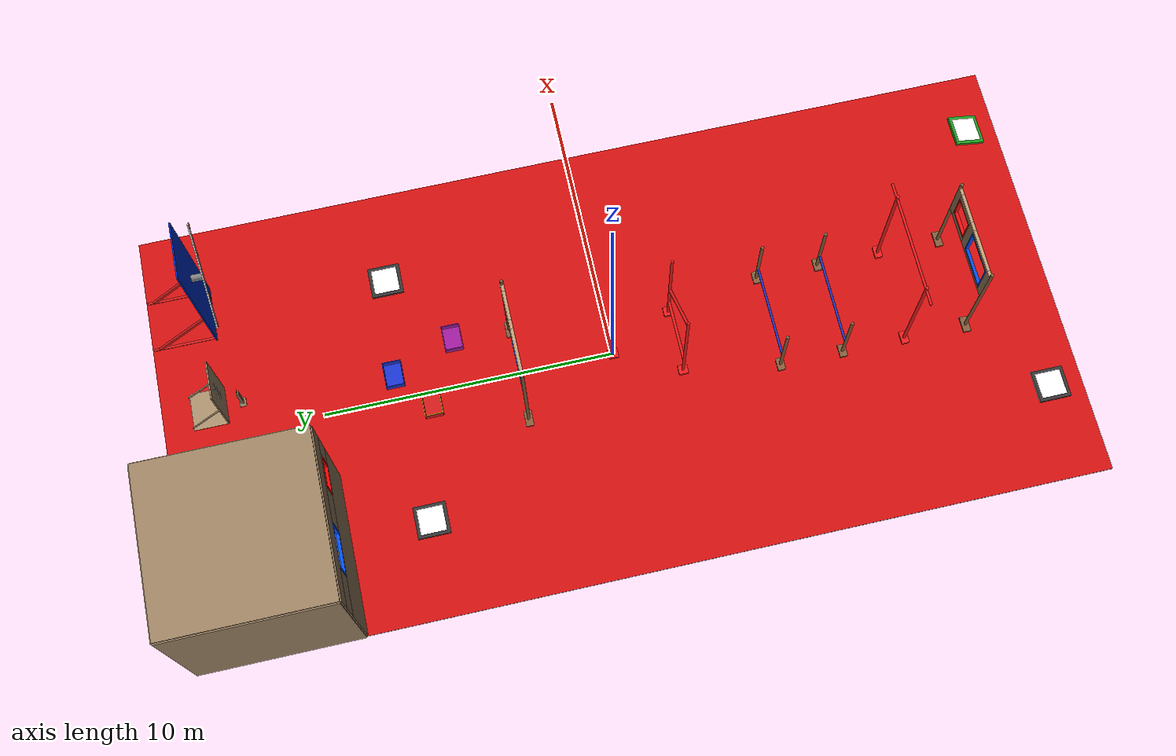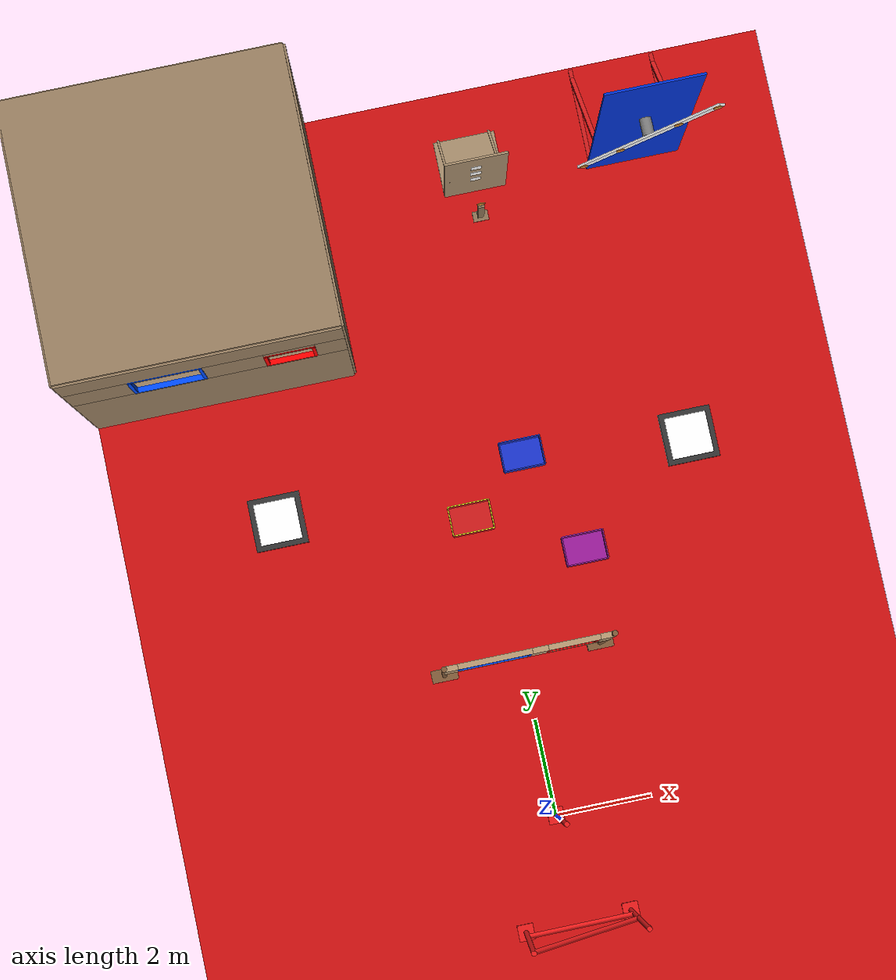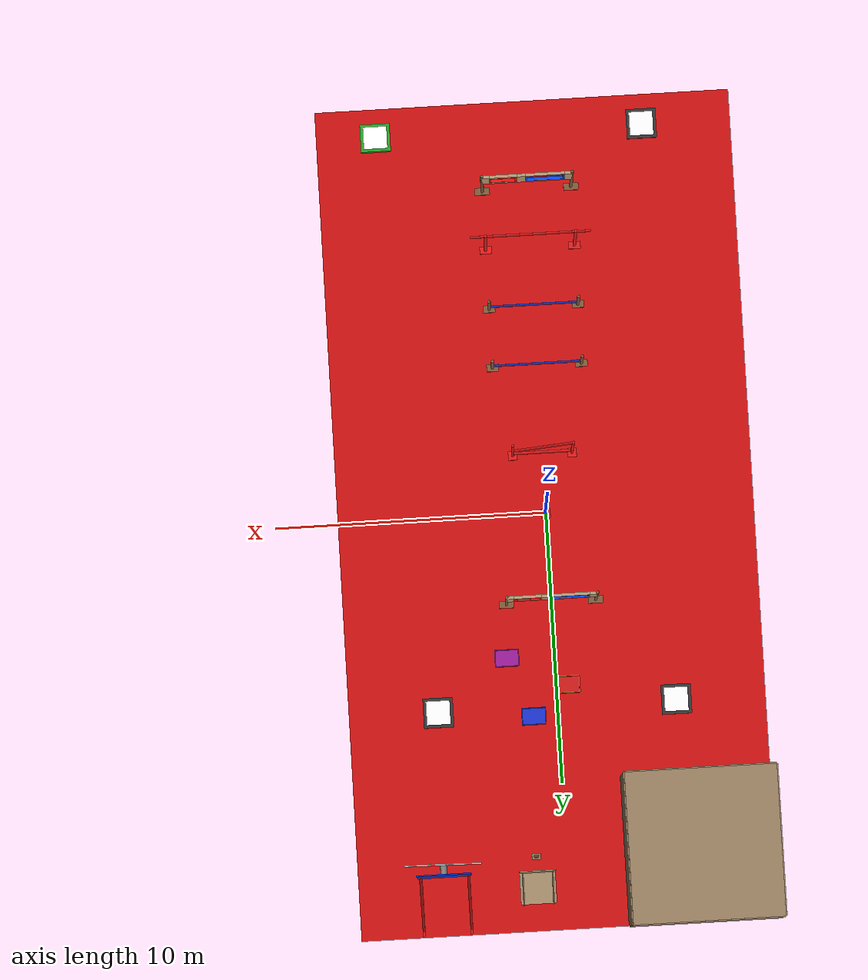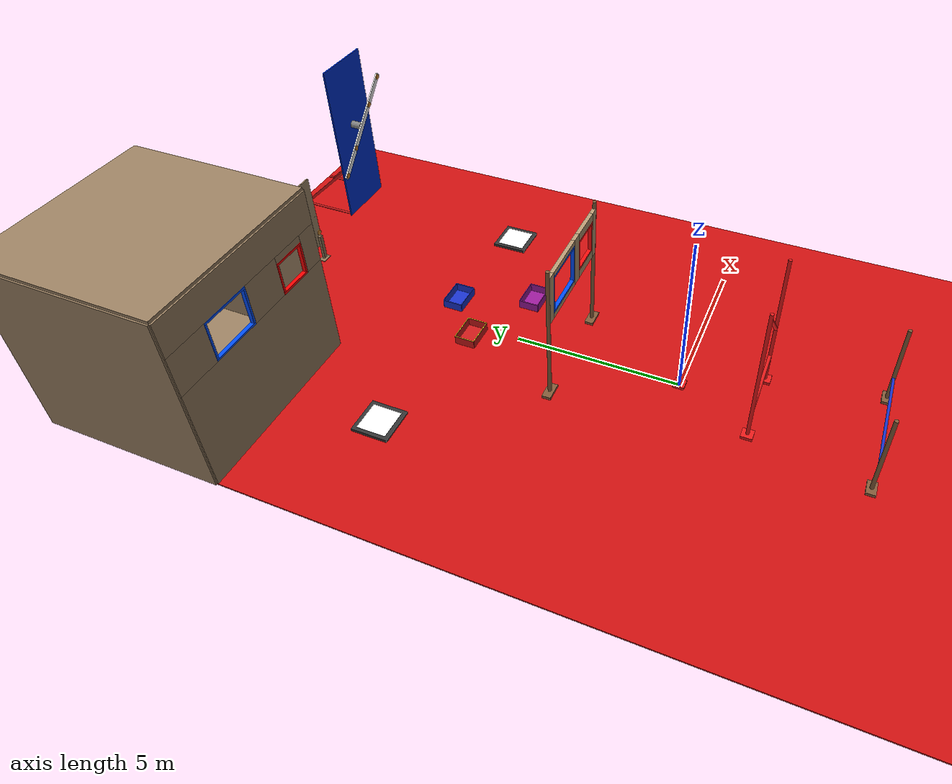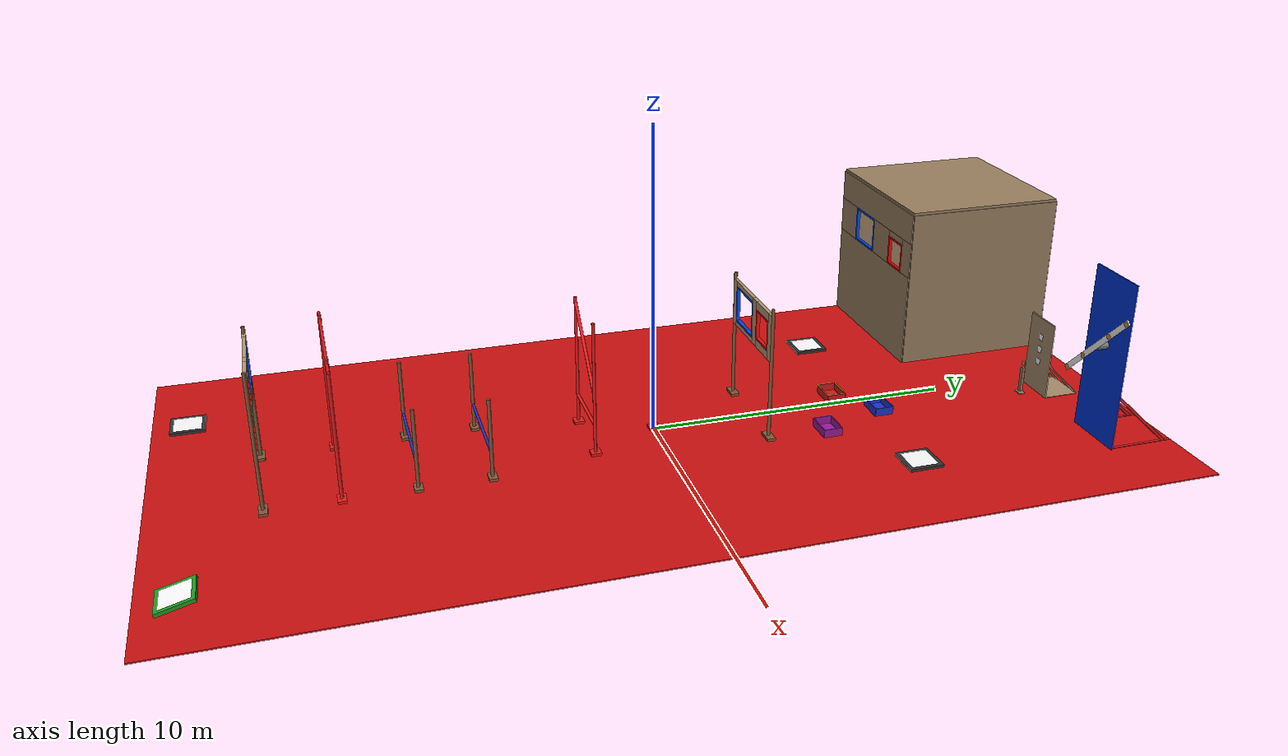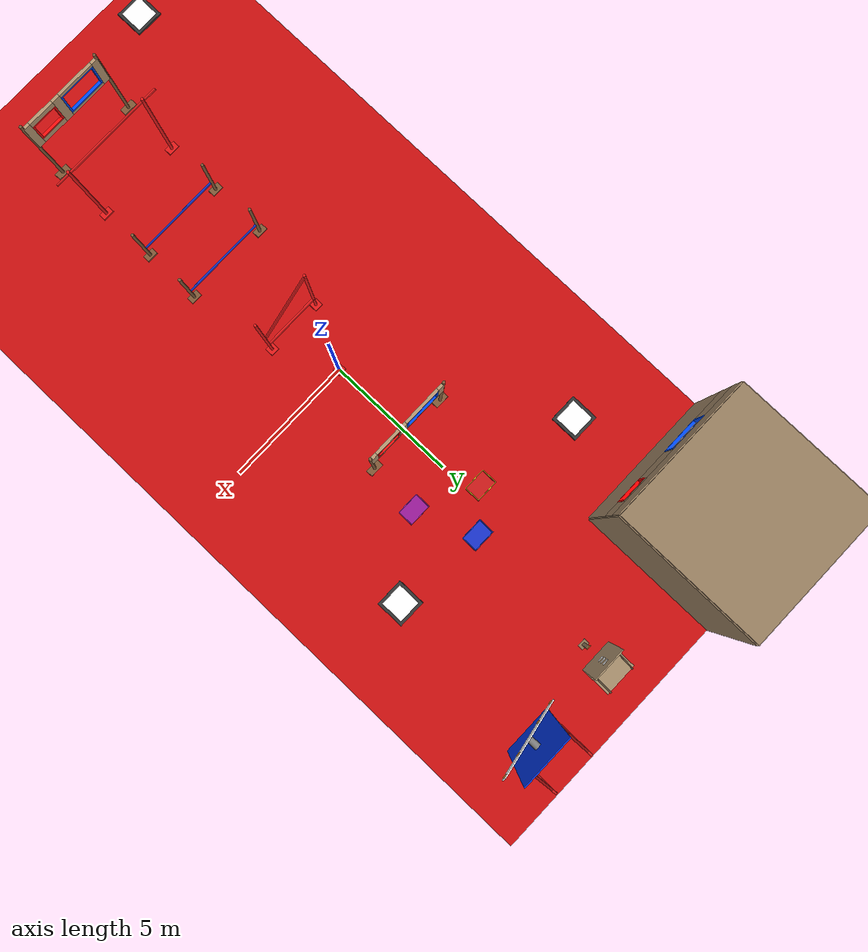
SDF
<sdf version="1.9">
 <world name="imav2026_scaled">
  <spherical_coordinates>
   <surface_model>EARTH_WGS84</surface_model>
   <latitude_deg>47.397742</latitude_deg>
   <longitude_deg>8.545594</longitude_deg>
   <elevation>488.0</elevation>
   <heading_deg>0</heading_deg>
  </spherical_coordinates>
  <physics type="ode">
   <max_step_size>0.004</max_step_size>
   <real_time_factor>1.0</real_time_factor>
   <real_time_update_rate>250</real_time_update_rate>
  </physics>
  <atmosphere type="adiabatic"/>
  <physics name="1ms" type="dart">
   <max_step_size>0.001</max_step_size>
   <real_time_factor>1.0</real_time_factor>
  </physics>
  <plugin filename="gz-sim-physics-system" name="gz::sim::systems::Physics"/>
  <plugin filename="gz-sim-user-commands-system" name="gz::sim::systems::UserCommands"/>
  <plugin filename="gz-sim-scene-broadcaster-system" name="gz::sim::systems::SceneBroadcaster"/>
  <plugin filename="gz-sim-contact-system" name="gz::sim::systems::Contact"/>
  <plugin filename="gz-sim-imu-system" name="gz::sim::systems::Imu"/>
  <plugin filename="gz-sim-air-pressure-system" name="gz::sim::systems::AirPressure"/>
  <plugin filename="gz-sim-magnetometer-system" name="gz::sim::systems::Magnetometer"/>
  <plugin filename="gz-sim-navsat-system" name="gz::sim::systems::NavSat"/>
  <plugin filename="gz-sim-sensors-system" name="gz::sim::systems::Sensors">
   <render_engine>ogre2</render_engine>
  </plugin>
  <scene>
   <ambient>0.6 0.6 0.6 1</ambient>
   <background>0.15 0.15 0.15 1</background>
   <shadows>true</shadows>
  </scene>
  <gravity>0 0 -9.81</gravity>
  <magnetic_field>6e-06 2.3e-05 -4.2e-05</magnetic_field>
  <light name="hall_sun" type="directional">
   <pose>0.0 0.0 22.0 0 0 0</pose>
   <diffuse>0.8 0.8 0.8 1</diffuse>
   <specular>0.2 0.2 0.2 1</specular>
   <direction>0.1 0.1 -1</direction>
  </light>
  <model name="arena_floor">
   <static>true</static>
   <link name="link">
    <collision name="col"><geometry><box><size>15.4 30.8 0.044</size></box></geometry></collision>
    <visual name="vis">
     <geometry><box><size>15.4 30.8 0.044</size></box></geometry>
     <material>
      <ambient>0.80 0.06 0.06 1</ambient>
      <diffuse>0.80 0.06 0.06 1</diffuse>
      <pbr><metal><roughness>0.8</roughness><metalness>0.0</metalness></metal></pbr>
     </material>
    </visual>
   </link>
  </model>
  <model name="room_floor">
   <static>true</static>
   <pose>-4.95 12.65 0.022 0 0 0</pose>
   <link name="link">
    <collision name="col"><geometry><box><size>5.5 5.5 0.044</size></box></geometry></collision>
    <visual name="v">
     <geometry><box><size>5.5 5.5 0.044</size></box></geometry>
     <material>
      <ambient>0.60 0.50 0.38 1</ambient>
      <diffuse>0.60 0.50 0.38 1</diffuse>
      <pbr><metal><roughness>0.8</roughness><metalness>0.0</metalness></metal></pbr>
     </material>
    </visual>
   </link>
  </model>
  <model name="room_N">
   <static>true</static>
   <pose>-4.95 15.4 2.75 0 0 0</pose>
   <link name="link">
    <collision name="col"><geometry><box><size>5.5 0.088 5.5</size></box></geometry></collision>
    <visual name="v">
     <geometry><box><size>5.5 0.088 5.5</size></box></geometry>
     <material>
      <ambient>0.60 0.50 0.38 1</ambient>
      <diffuse>0.60 0.50 0.38 1</diffuse>
      <pbr><metal><roughness>0.8</roughness><metalness>0.0</metalness></metal></pbr>
     </material>
    </visual>
   </link>
  </model>
  <model name="room_W">
   <static>true</static>
   <pose>-7.7 12.65 2.75 0 0 0</pose>
   <link name="link">
    <collision name="col"><geometry><box><size>0.088 5.5 5.5</size></box></geometry></collision>
    <visual name="v">
     <geometry><box><size>0.088 5.5 5.5</size></box></geometry>
     <material>
      <ambient>0.60 0.50 0.38 1</ambient>
      <diffuse>0.60 0.50 0.38 1</diffuse>
      <pbr><metal><roughness>0.8</roughness><metalness>0.0</metalness></metal></pbr>
     </material>
    </visual>
   </link>
  </model>
  <model name="room_E">
   <static>true</static>
   <pose>-2.2 12.65 2.75 0 0 0</pose>
   <link name="link">
    <collision name="col"><geometry><box><size>0.088 5.5 5.5</size></box></geometry></collision>
    <visual name="v">
     <geometry><box><size>0.088 5.5 5.5</size></box></geometry>
     <material>
      <ambient>0.60 0.50 0.38 1</ambient>
      <diffuse>0.60 0.50 0.38 1</diffuse>
      <pbr><metal><roughness>0.8</roughness><metalness>0.0</metalness></metal></pbr>
     </material>
    </visual>
   </link>
  </model>
  <model name="room_ceil">
   <static>true</static>
   <pose>-4.95 12.65 5.544 0 0 0</pose>
   <link name="link">
    <collision name="col"><geometry><box><size>5.5 5.5 0.088</size></box></geometry></collision>
    <visual name="v">
     <geometry><box><size>5.5 5.5 0.088</size></box></geometry>
     <material>
      <ambient>0.60 0.50 0.38 1</ambient>
      <diffuse>0.60 0.50 0.38 1</diffuse>
      <pbr><metal><roughness>0.8</roughness><metalness>0.0</metalness></metal></pbr>
     </material>
    </visual>
   </link>
  </model>
  <model name="room_S_bot">
   <static>true</static>
   <pose>-4.95 9.9 1.617 0 0 0</pose>
   <link name="link">
    <collision name="col"><geometry><box><size>5.5 0.088 3.234</size></box></geometry></collision>
    <visual name="v">
     <geometry><box><size>5.5 0.088 3.234</size></box></geometry>
     <material>
      <ambient>0.60 0.50 0.38 1</ambient>
      <diffuse>0.60 0.50 0.38 1</diffuse>
      <pbr><metal><roughness>0.8</roughness><metalness>0.0</metalness></metal></pbr>
     </material>
    </visual>
   </link>
  </model>
  <model name="room_S_top">
   <static>true</static>
   <pose>-4.95 9.9 4.983 0 0 0</pose>
   <link name="link">
    <collision name="col"><geometry><box><size>5.5 0.088 1.034</size></box></geometry></collision>
    <visual name="v">
     <geometry><box><size>5.5 0.088 1.034</size></box></geometry>
     <material>
      <ambient>0.60 0.50 0.38 1</ambient>
      <diffuse>0.60 0.50 0.38 1</diffuse>
      <pbr><metal><roughness>0.8</roughness><metalness>0.0</metalness></metal></pbr>
     </material>
    </visual>
   </link>
  </model>
  <model name="room_S_seg_L">
   <static>true</static>
   <pose>-7.073 9.9 3.85 0 0 0</pose>
   <link name="link">
    <collision name="col"><geometry><box><size>1.254 0.088 1.232</size></box></geometry></collision>
    <visual name="v">
     <geometry><box><size>1.254 0.088 1.232</size></box></geometry>
     <material>
      <ambient>0.60 0.50 0.38 1</ambient>
      <diffuse>0.60 0.50 0.38 1</diffuse>
      <pbr><metal><roughness>0.8</roughness><metalness>0.0</metalness></metal></pbr>
     </material>
    </visual>
   </link>
  </model>
  <model name="room_S_seg_M">
   <static>true</static>
   <pose>-4.4 9.9 3.85 0 0 0</pose>
   <link name="link">
    <collision name="col"><geometry><box><size>1.188 0.088 1.232</size></box></geometry></collision>
    <visual name="v">
     <geometry><box><size>1.188 0.088 1.232</size></box></geometry>
     <material>
      <ambient>0.60 0.50 0.38 1</ambient>
      <diffuse>0.60 0.50 0.38 1</diffuse>
      <pbr><metal><roughness>0.8</roughness><metalness>0.0</metalness></metal></pbr>
     </material>
    </visual>
   </link>
  </model>
  <model name="room_S_seg_R">
   <static>true</static>
   <pose>-2.497 9.9 3.85 0 0 0</pose>
   <link name="link">
    <collision name="col"><geometry><box><size>0.594 0.088 1.232</size></box></geometry></collision>
    <visual name="v">
     <geometry><box><size>0.594 0.088 1.232</size></box></geometry>
     <material>
      <ambient>0.60 0.50 0.38 1</ambient>
      <diffuse>0.60 0.50 0.38 1</diffuse>
      <pbr><metal><roughness>0.8</roughness><metalness>0.0</metalness></metal></pbr>
     </material>
    </visual>
   </link>
  </model>
  <model name="room_S_seg_above_red">
   <static>true</static>
   <pose>-3.3 9.9 4.356 0 0 0</pose>
   <link name="link">
    <collision name="col"><geometry><box><size>1.012 0.088 0.22</size></box></geometry></collision>
    <visual name="v">
     <geometry><box><size>1.012 0.088 0.22</size></box></geometry>
     <material>
      <ambient>0.60 0.50 0.38 1</ambient>
      <diffuse>0.60 0.50 0.38 1</diffuse>
      <pbr><metal><roughness>0.8</roughness><metalness>0.0</metalness></metal></pbr>
     </material>
    </visual>
   </link>
  </model>
  <model name="room_blue_top">
   <static>true</static>
   <pose>-5.72 9.9 4.433 0 0 0</pose>
   <link name="link">
    <collision name="col"><geometry><box><size>1.452 0.11 0.066</size></box></geometry></collision>
    <visual name="v">
     <geometry><box><size>1.452 0.11 0.066</size></box></geometry>
     <material>
      <ambient>0.0 0.3 1.0 1</ambient>
      <diffuse>0.0 0.3 1.0 1</diffuse>
      <pbr><metal><roughness>0.5</roughness><metalness>0.0</metalness></metal></pbr>
     </material>
    </visual>
   </link>
  </model>
  <model name="room_blue_bot">
   <static>true</static>
   <pose>-5.72 9.9 3.267 0 0 0</pose>
   <link name="link">
    <collision name="col"><geometry><box><size>1.452 0.11 0.066</size></box></geometry></collision>
    <visual name="v">
     <geometry><box><size>1.452 0.11 0.066</size></box></geometry>
     <material>
      <ambient>0.0 0.3 1.0 1</ambient>
      <diffuse>0.0 0.3 1.0 1</diffuse>
      <pbr><metal><roughness>0.5</roughness><metalness>0.0</metalness></metal></pbr>
     </material>
    </visual>
   </link>
  </model>
  <model name="room_blue_L">
   <static>true</static>
   <pose>-6.413 9.9 3.85 0 0 0</pose>
   <link name="link">
    <collision name="col"><geometry><box><size>0.066 0.11 1.1</size></box></geometry></collision>
    <visual name="v">
     <geometry><box><size>0.066 0.11 1.1</size></box></geometry>
     <material>
      <ambient>0.0 0.3 1.0 1</ambient>
      <diffuse>0.0 0.3 1.0 1</diffuse>
      <pbr><metal><roughness>0.5</roughness><metalness>0.0</metalness></metal></pbr>
     </material>
    </visual>
   </link>
  </model>
  <model name="room_blue_R">
   <static>true</static>
   <pose>-5.027 9.9 3.85 0 0 0</pose>
   <link name="link">
    <collision name="col"><geometry><box><size>0.066 0.11 1.1</size></box></geometry></collision>
    <visual name="v">
     <geometry><box><size>0.066 0.11 1.1</size></box></geometry>
     <material>
      <ambient>0.0 0.3 1.0 1</ambient>
      <diffuse>0.0 0.3 1.0 1</diffuse>
      <pbr><metal><roughness>0.5</roughness><metalness>0.0</metalness></metal></pbr>
     </material>
    </visual>
   </link>
  </model>
  <model name="room_red_top">
   <static>true</static>
   <pose>-3.3 9.9 4.213 0 0 0</pose>
   <link name="link">
    <collision name="col"><geometry><box><size>1.012 0.11 0.066</size></box></geometry></collision>
    <visual name="v">
     <geometry><box><size>1.012 0.11 0.066</size></box></geometry>
     <material>
      <ambient>1.0 0.0 0.0 1</ambient>
      <diffuse>1.0 0.0 0.0 1</diffuse>
      <pbr><metal><roughness>0.5</roughness><metalness>0.0</metalness></metal></pbr>
     </material>
    </visual>
   </link>
  </model>
  <model name="room_red_bot">
   <static>true</static>
   <pose>-3.3 9.9 3.267 0 0 0</pose>
   <link name="link">
    <collision name="col"><geometry><box><size>1.012 0.11 0.066</size></box></geometry></collision>
    <visual name="v">
     <geometry><box><size>1.012 0.11 0.066</size></box></geometry>
     <material>
      <ambient>1.0 0.0 0.0 1</ambient>
      <diffuse>1.0 0.0 0.0 1</diffuse>
      <pbr><metal><roughness>0.5</roughness><metalness>0.0</metalness></metal></pbr>
     </material>
    </visual>
   </link>
  </model>
  <model name="room_red_L">
   <static>true</static>
   <pose>-3.773 9.9 3.74 0 0 0</pose>
   <link name="link">
    <collision name="col"><geometry><box><size>0.066 0.11 0.88</size></box></geometry></collision>
    <visual name="v">
     <geometry><box><size>0.066 0.11 0.88</size></box></geometry>
     <material>
      <ambient>1.0 0.0 0.0 1</ambient>
      <diffuse>1.0 0.0 0.0 1</diffuse>
      <pbr><metal><roughness>0.5</roughness><metalness>0.0</metalness></metal></pbr>
     </material>
    </visual>
   </link>
  </model>
  <model name="room_red_R">
   <static>true</static>
   <pose>-2.827 9.9 3.74 0 0 0</pose>
   <link name="link">
    <collision name="col"><geometry><box><size>0.066 0.11 0.88</size></box></geometry></collision>
    <visual name="v">
     <geometry><box><size>0.066 0.11 0.88</size></box></geometry>
     <material>
      <ambient>1.0 0.0 0.0 1</ambient>
      <diffuse>1.0 0.0 0.0 1</diffuse>
      <pbr><metal><roughness>0.5</roughness><metalness>0.0</metalness></metal></pbr>
     </material>
    </visual>
   </link>
  </model>
  <model name="obs_wall_leg_L">
   <static>true</static>
   <pose>-1.65 3.3 2.2 0 0 0</pose>
   <link name="link">
    <collision name="col">
     <geometry><cylinder><radius>0.055</radius><length>4.4</length></cylinder></geometry>
    </collision>
    <visual name="v">
     <geometry><cylinder><radius>0.055</radius><length>4.4</length></cylinder></geometry>
     <material>
      <ambient>0.50 0.35 0.22 1</ambient>
      <diffuse>0.50 0.35 0.22 1</diffuse>
      <pbr><metal><roughness>0.8</roughness><metalness>0.0</metalness></metal></pbr>
     </material>
    </visual>
   </link>
  </model>
  <model name="obs_wall_foot_L">
   <static>true</static>
   <pose>-1.65 3.3 0.055 0 0 0</pose>
   <link name="link">
    <collision name="col"><geometry><box><size>0.55 0.264 0.11</size></box></geometry></collision>
    <visual name="v">
     <geometry><box><size>0.55 0.264 0.11</size></box></geometry>
     <material>
      <ambient>0.50 0.35 0.22 1</ambient>
      <diffuse>0.50 0.35 0.22 1</diffuse>
      <pbr><metal><roughness>0.8</roughness><metalness>0.0</metalness></metal></pbr>
     </material>
    </visual>
   </link>
  </model>
  <model name="obs_wall_leg_R">
   <static>true</static>
   <pose>1.65 3.3 2.2 0 0 0</pose>
   <link name="link">
    <collision name="col">
     <geometry><cylinder><radius>0.055</radius><length>4.4</length></cylinder></geometry>
    </collision>
    <visual name="v">
     <geometry><cylinder><radius>0.055</radius><length>4.4</length></cylinder></geometry>
     <material>
      <ambient>0.50 0.35 0.22 1</ambient>
      <diffuse>0.50 0.35 0.22 1</diffuse>
      <pbr><metal><roughness>0.8</roughness><metalness>0.0</metalness></metal></pbr>
     </material>
    </visual>
   </link>
  </model>
  <model name="obs_wall_foot_R">
   <static>true</static>
   <pose>1.65 3.3 0.055 0 0 0</pose>
   <link name="link">
    <collision name="col"><geometry><box><size>0.55 0.264 0.11</size></box></geometry></collision>
    <visual name="v">
     <geometry><box><size>0.55 0.264 0.11</size></box></geometry>
     <material>
      <ambient>0.50 0.35 0.22 1</ambient>
      <diffuse>0.50 0.35 0.22 1</diffuse>
      <pbr><metal><roughness>0.8</roughness><metalness>0.0</metalness></metal></pbr>
     </material>
    </visual>
   </link>
  </model>
  <model name="obs_wall_bd_L">
   <static>true</static>
   <pose>-1.518 3.3 3.41 0 0 0</pose>
   <link name="link">
    <collision name="col"><geometry><box><size>0.264 0.11 1.54</size></box></geometry></collision>
    <visual name="v">
     <geometry><box><size>0.264 0.11 1.54</size></box></geometry>
     <material>
      <ambient>0.72 0.60 0.45 1</ambient>
      <diffuse>0.72 0.60 0.45 1</diffuse>
      <pbr><metal><roughness>0.8</roughness><metalness>0.0</metalness></metal></pbr>
     </material>
    </visual>
   </link>
  </model>
  <model name="obs_wall_bd_M">
   <static>true</static>
   <pose>0.22 3.3 3.41 0 0 0</pose>
   <link name="link">
    <collision name="col"><geometry><box><size>0.308 0.11 1.54</size></box></geometry></collision>
    <visual name="v">
     <geometry><box><size>0.308 0.11 1.54</size></box></geometry>
     <material>
      <ambient>0.72 0.60 0.45 1</ambient>
      <diffuse>0.72 0.60 0.45 1</diffuse>
      <pbr><metal><roughness>0.8</roughness><metalness>0.0</metalness></metal></pbr>
     </material>
    </visual>
   </link>
  </model>
  <model name="obs_wall_bd_R">
   <static>true</static>
   <pose>1.518 3.3 3.41 0 0 0</pose>
   <link name="link">
    <collision name="col"><geometry><box><size>0.264 0.11 1.54</size></box></geometry></collision>
    <visual name="v">
     <geometry><box><size>0.264 0.11 1.54</size></box></geometry>
     <material>
      <ambient>0.72 0.60 0.45 1</ambient>
      <diffuse>0.72 0.60 0.45 1</diffuse>
      <pbr><metal><roughness>0.8</roughness><metalness>0.0</metalness></metal></pbr>
     </material>
    </visual>
   </link>
  </model>
  <model name="obs_wall_bd_B_blue">
   <static>true</static>
   <pose>-0.66 3.3 2.717 0 0 0</pose>
   <link name="link">
    <collision name="col"><geometry><box><size>1.452 0.11 0.154</size></box></geometry></collision>
    <visual name="v">
     <geometry><box><size>1.452 0.11 0.154</size></box></geometry>
     <material>
      <ambient>0.72 0.60 0.45 1</ambient>
      <diffuse>0.72 0.60 0.45 1</diffuse>
      <pbr><metal><roughness>0.8</roughness><metalness>0.0</metalness></metal></pbr>
     </material>
    </visual>
   </link>
  </model>
  <model name="obs_wall_bd_T_blue">
   <static>true</static>
   <pose>-0.66 3.3 4.103 0 0 0</pose>
   <link name="link">
    <collision name="col"><geometry><box><size>1.452 0.11 0.154</size></box></geometry></collision>
    <visual name="v">
     <geometry><box><size>1.452 0.11 0.154</size></box></geometry>
     <material>
      <ambient>0.72 0.60 0.45 1</ambient>
      <diffuse>0.72 0.60 0.45 1</diffuse>
      <pbr><metal><roughness>0.8</roughness><metalness>0.0</metalness></metal></pbr>
     </material>
    </visual>
   </link>
  </model>
  <model name="obs_wall_bd_B_red">
   <static>true</static>
   <pose>0.88 3.3 2.772 0 0 0</pose>
   <link name="link">
    <collision name="col"><geometry><box><size>1.012 0.11 0.264</size></box></geometry></collision>
    <visual name="v">
     <geometry><box><size>1.012 0.11 0.264</size></box></geometry>
     <material>
      <ambient>0.72 0.60 0.45 1</ambient>
      <diffuse>0.72 0.60 0.45 1</diffuse>
      <pbr><metal><roughness>0.8</roughness><metalness>0.0</metalness></metal></pbr>
     </material>
    </visual>
   </link>
  </model>
  <model name="obs_wall_bd_T_red">
   <static>true</static>
   <pose>0.88 3.3 4.048 0 0 0</pose>
   <link name="link">
    <collision name="col"><geometry><box><size>1.012 0.11 0.264</size></box></geometry></collision>
    <visual name="v">
     <geometry><box><size>1.012 0.11 0.264</size></box></geometry>
     <material>
      <ambient>0.72 0.60 0.45 1</ambient>
      <diffuse>0.72 0.60 0.45 1</diffuse>
      <pbr><metal><roughness>0.8</roughness><metalness>0.0</metalness></metal></pbr>
     </material>
    </visual>
   </link>
  </model>
  <model name="obs_wall_blue_top">
   <static>true</static>
   <pose>-0.66 3.3 3.993 0 0 0</pose>
   <link name="link">
    <collision name="col"><geometry><box><size>1.452 0.11 0.066</size></box></geometry></collision>
    <visual name="v">
     <geometry><box><size>1.452 0.11 0.066</size></box></geometry>
     <material>
      <ambient>0.0 0.3 1.0 1</ambient>
      <diffuse>0.0 0.3 1.0 1</diffuse>
      <pbr><metal><roughness>0.5</roughness><metalness>0.0</metalness></metal></pbr>
     </material>
    </visual>
   </link>
  </model>
  <model name="obs_wall_blue_bot">
   <static>true</static>
   <pose>-0.66 3.3 2.827 0 0 0</pose>
   <link name="link">
    <collision name="col"><geometry><box><size>1.452 0.11 0.066</size></box></geometry></collision>
    <visual name="v">
     <geometry><box><size>1.452 0.11 0.066</size></box></geometry>
     <material>
      <ambient>0.0 0.3 1.0 1</ambient>
      <diffuse>0.0 0.3 1.0 1</diffuse>
      <pbr><metal><roughness>0.5</roughness><metalness>0.0</metalness></metal></pbr>
     </material>
    </visual>
   </link>
  </model>
  <model name="obs_wall_blue_L">
   <static>true</static>
   <pose>-1.353 3.3 3.41 0 0 0</pose>
   <link name="link">
    <collision name="col"><geometry><box><size>0.066 0.11 1.1</size></box></geometry></collision>
    <visual name="v">
     <geometry><box><size>0.066 0.11 1.1</size></box></geometry>
     <material>
      <ambient>0.0 0.3 1.0 1</ambient>
      <diffuse>0.0 0.3 1.0 1</diffuse>
      <pbr><metal><roughness>0.5</roughness><metalness>0.0</metalness></metal></pbr>
     </material>
    </visual>
   </link>
  </model>
  <model name="obs_wall_blue_R">
   <static>true</static>
   <pose>0.033 3.3 3.41 0 0 0</pose>
   <link name="link">
    <collision name="col"><geometry><box><size>0.066 0.11 1.1</size></box></geometry></collision>
    <visual name="v">
     <geometry><box><size>0.066 0.11 1.1</size></box></geometry>
     <material>
      <ambient>0.0 0.3 1.0 1</ambient>
      <diffuse>0.0 0.3 1.0 1</diffuse>
      <pbr><metal><roughness>0.5</roughness><metalness>0.0</metalness></metal></pbr>
     </material>
    </visual>
   </link>
  </model>
  <model name="obs_wall_red_top">
   <static>true</static>
   <pose>0.88 3.3 3.883 0 0 0</pose>
   <link name="link">
    <collision name="col"><geometry><box><size>1.012 0.11 0.066</size></box></geometry></collision>
    <visual name="v">
     <geometry><box><size>1.012 0.11 0.066</size></box></geometry>
     <material>
      <ambient>1.0 0.05 0.05 1</ambient>
      <diffuse>1.0 0.05 0.05 1</diffuse>
      <pbr><metal><roughness>0.5</roughness><metalness>0.0</metalness></metal></pbr>
     </material>
    </visual>
   </link>
  </model>
  <model name="obs_wall_red_bot">
   <static>true</static>
   <pose>0.88 3.3 2.937 0 0 0</pose>
   <link name="link">
    <collision name="col"><geometry><box><size>1.012 0.11 0.066</size></box></geometry></collision>
    <visual name="v">
     <geometry><box><size>1.012 0.11 0.066</size></box></geometry>
     <material>
      <ambient>1.0 0.05 0.05 1</ambient>
      <diffuse>1.0 0.05 0.05 1</diffuse>
      <pbr><metal><roughness>0.5</roughness><metalness>0.0</metalness></metal></pbr>
     </material>
    </visual>
   </link>
  </model>
  <model name="obs_wall_red_L">
   <static>true</static>
   <pose>0.407 3.3 3.41 0 0 0</pose>
   <link name="link">
    <collision name="col"><geometry><box><size>0.066 0.11 0.88</size></box></geometry></collision>
    <visual name="v">
     <geometry><box><size>0.066 0.11 0.88</size></box></geometry>
     <material>
      <ambient>1.0 0.05 0.05 1</ambient>
      <diffuse>1.0 0.05 0.05 1</diffuse>
      <pbr><metal><roughness>0.5</roughness><metalness>0.0</metalness></metal></pbr>
     </material>
    </visual>
   </link>
  </model>
  <model name="obs_wall_red_R">
   <static>true</static>
   <pose>1.353 3.3 3.41 0 0 0</pose>
   <link name="link">
    <collision name="col"><geometry><box><size>0.066 0.11 0.88</size></box></geometry></collision>
    <visual name="v">
     <geometry><box><size>0.066 0.11 0.88</size></box></geometry>
     <material>
      <ambient>1.0 0.05 0.05 1</ambient>
      <diffuse>1.0 0.05 0.05 1</diffuse>
      <pbr><metal><roughness>0.5</roughness><metalness>0.0</metalness></metal></pbr>
     </material>
    </visual>
   </link>
  </model>
  <model name="exit_wall_leg_L">
   <static>true</static>
   <pose>-1.65 -12.1 2.2 0 0 0</pose>
   <link name="link">
    <collision name="col">
     <geometry><cylinder><radius>0.055</radius><length>4.4</length></cylinder></geometry>
    </collision>
    <visual name="v">
     <geometry><cylinder><radius>0.055</radius><length>4.4</length></cylinder></geometry>
     <material>
      <ambient>0.50 0.35 0.22 1</ambient>
      <diffuse>0.50 0.35 0.22 1</diffuse>
      <pbr><metal><roughness>0.8</roughness><metalness>0.0</metalness></metal></pbr>
     </material>
    </visual>
   </link>
  </model>
  <model name="exit_wall_foot_L">
   <static>true</static>
   <pose>-1.65 -12.1 0.055 0 0 0</pose>
   <link name="link">
    <collision name="col"><geometry><box><size>0.55 0.264 0.11</size></box></geometry></collision>
    <visual name="v">
     <geometry><box><size>0.55 0.264 0.11</size></box></geometry>
     <material>
      <ambient>0.50 0.35 0.22 1</ambient>
      <diffuse>0.50 0.35 0.22 1</diffuse>
      <pbr><metal><roughness>0.8</roughness><metalness>0.0</metalness></metal></pbr>
     </material>
    </visual>
   </link>
  </model>
  <model name="exit_wall_leg_R">
   <static>true</static>
   <pose>1.65 -12.1 2.2 0 0 0</pose>
   <link name="link">
    <collision name="col">
     <geometry><cylinder><radius>0.055</radius><length>4.4</length></cylinder></geometry>
    </collision>
    <visual name="v">
     <geometry><cylinder><radius>0.055</radius><length>4.4</length></cylinder></geometry>
     <material>
      <ambient>0.50 0.35 0.22 1</ambient>
      <diffuse>0.50 0.35 0.22 1</diffuse>
      <pbr><metal><roughness>0.8</roughness><metalness>0.0</metalness></metal></pbr>
     </material>
    </visual>
   </link>
  </model>
  <model name="exit_wall_foot_R">
   <static>true</static>
   <pose>1.65 -12.1 0.055 0 0 0</pose>
   <link name="link">
    <collision name="col"><geometry><box><size>0.55 0.264 0.11</size></box></geometry></collision>
    <visual name="v">
     <geometry><box><size>0.55 0.264 0.11</size></box></geometry>
     <material>
      <ambient>0.50 0.35 0.22 1</ambient>
      <diffuse>0.50 0.35 0.22 1</diffuse>
      <pbr><metal><roughness>0.8</roughness><metalness>0.0</metalness></metal></pbr>
     </material>
    </visual>
   </link>
  </model>
  <model name="exit_wall_bd_L">
   <static>true</static>
   <pose>-1.518 -12.1 3.41 0 0 0</pose>
   <link name="link">
    <collision name="col"><geometry><box><size>0.264 0.11 1.54</size></box></geometry></collision>
    <visual name="v">
     <geometry><box><size>0.264 0.11 1.54</size></box></geometry>
     <material>
      <ambient>0.72 0.60 0.45 1</ambient>
      <diffuse>0.72 0.60 0.45 1</diffuse>
      <pbr><metal><roughness>0.8</roughness><metalness>0.0</metalness></metal></pbr>
     </material>
    </visual>
   </link>
  </model>
  <model name="exit_wall_bd_M">
   <static>true</static>
   <pose>0.22 -12.1 3.41 0 0 0</pose>
   <link name="link">
    <collision name="col"><geometry><box><size>0.308 0.11 1.54</size></box></geometry></collision>
    <visual name="v">
     <geometry><box><size>0.308 0.11 1.54</size></box></geometry>
     <material>
      <ambient>0.72 0.60 0.45 1</ambient>
      <diffuse>0.72 0.60 0.45 1</diffuse>
      <pbr><metal><roughness>0.8</roughness><metalness>0.0</metalness></metal></pbr>
     </material>
    </visual>
   </link>
  </model>
  <model name="exit_wall_bd_R">
   <static>true</static>
   <pose>1.518 -12.1 3.41 0 0 0</pose>
   <link name="link">
    <collision name="col"><geometry><box><size>0.264 0.11 1.54</size></box></geometry></collision>
    <visual name="v">
     <geometry><box><size>0.264 0.11 1.54</size></box></geometry>
     <material>
      <ambient>0.72 0.60 0.45 1</ambient>
      <diffuse>0.72 0.60 0.45 1</diffuse>
      <pbr><metal><roughness>0.8</roughness><metalness>0.0</metalness></metal></pbr>
     </material>
    </visual>
   </link>
  </model>
  <model name="exit_wall_bd_B_blue">
   <static>true</static>
   <pose>-0.66 -12.1 2.717 0 0 0</pose>
   <link name="link">
    <collision name="col"><geometry><box><size>1.452 0.11 0.154</size></box></geometry></collision>
    <visual name="v">
     <geometry><box><size>1.452 0.11 0.154</size></box></geometry>
     <material>
      <ambient>0.72 0.60 0.45 1</ambient>
      <diffuse>0.72 0.60 0.45 1</diffuse>
      <pbr><metal><roughness>0.8</roughness><metalness>0.0</metalness></metal></pbr>
     </material>
    </visual>
   </link>
  </model>
  <model name="exit_wall_bd_T_blue">
   <static>true</static>
   <pose>-0.66 -12.1 4.103 0 0 0</pose>
   <link name="link">
    <collision name="col"><geometry><box><size>1.452 0.11 0.154</size></box></geometry></collision>
    <visual name="v">
     <geometry><box><size>1.452 0.11 0.154</size></box></geometry>
     <material>
      <ambient>0.72 0.60 0.45 1</ambient>
      <diffuse>0.72 0.60 0.45 1</diffuse>
      <pbr><metal><roughness>0.8</roughness><metalness>0.0</metalness></metal></pbr>
     </material>
    </visual>
   </link>
  </model>
  <model name="exit_wall_bd_B_red">
   <static>true</static>
   <pose>0.88 -12.1 2.772 0 0 0</pose>
   <link name="link">
    <collision name="col"><geometry><box><size>1.012 0.11 0.264</size></box></geometry></collision>
    <visual name="v">
     <geometry><box><size>1.012 0.11 0.264</size></box></geometry>
     <material>
      <ambient>0.72 0.60 0.45 1</ambient>
      <diffuse>0.72 0.60 0.45 1</diffuse>
      <pbr><metal><roughness>0.8</roughness><metalness>0.0</metalness></metal></pbr>
     </material>
    </visual>
   </link>
  </model>
  <model name="exit_wall_bd_T_red">
   <static>true</static>
   <pose>0.88 -12.1 4.048 0 0 0</pose>
   <link name="link">
    <collision name="col"><geometry><box><size>1.012 0.11 0.264</size></box></geometry></collision>
    <visual name="v">
     <geometry><box><size>1.012 0.11 0.264</size></box></geometry>
     <material>
      <ambient>0.72 0.60 0.45 1</ambient>
      <diffuse>0.72 0.60 0.45 1</diffuse>
      <pbr><metal><roughness>0.8</roughness><metalness>0.0</metalness></metal></pbr>
     </material>
    </visual>
   </link>
  </model>
  <model name="exit_wall_blue_top">
   <static>true</static>
   <pose>-0.66 -12.1 3.993 0 0 0</pose>
   <link name="link">
    <collision name="col"><geometry><box><size>1.452 0.11 0.066</size></box></geometry></collision>
    <visual name="v">
     <geometry><box><size>1.452 0.11 0.066</size></box></geometry>
     <material>
      <ambient>0.0 0.3 1.0 1</ambient>
      <diffuse>0.0 0.3 1.0 1</diffuse>
      <pbr><metal><roughness>0.5</roughness><metalness>0.0</metalness></metal></pbr>
     </material>
    </visual>
   </link>
  </model>
  <model name="exit_wall_blue_bot">
   <static>true</static>
   <pose>-0.66 -12.1 2.827 0 0 0</pose>
   <link name="link">
    <collision name="col"><geometry><box><size>1.452 0.11 0.066</size></box></geometry></collision>
    <visual name="v">
     <geometry><box><size>1.452 0.11 0.066</size></box></geometry>
     <material>
      <ambient>0.0 0.3 1.0 1</ambient>
      <diffuse>0.0 0.3 1.0 1</diffuse>
      <pbr><metal><roughness>0.5</roughness><metalness>0.0</metalness></metal></pbr>
     </material>
    </visual>
   </link>
  </model>
  <model name="exit_wall_blue_L">
   <static>true</static>
   <pose>-1.353 -12.1 3.41 0 0 0</pose>
   <link name="link">
    <collision name="col"><geometry><box><size>0.066 0.11 1.1</size></box></geometry></collision>
    <visual name="v">
     <geometry><box><size>0.066 0.11 1.1</size></box></geometry>
     <material>
      <ambient>0.0 0.3 1.0 1</ambient>
      <diffuse>0.0 0.3 1.0 1</diffuse>
      <pbr><metal><roughness>0.5</roughness><metalness>0.0</metalness></metal></pbr>
     </material>
    </visual>
   </link>
  </model>
  <model name="exit_wall_blue_R">
   <static>true</static>
   <pose>0.033 -12.1 3.41 0 0 0</pose>
   <link name="link">
    <collision name="col"><geometry><box><size>0.066 0.11 1.1</size></box></geometry></collision>
    <visual name="v">
     <geometry><box><size>0.066 0.11 1.1</size></box></geometry>
     <material>
      <ambient>0.0 0.3 1.0 1</ambient>
      <diffuse>0.0 0.3 1.0 1</diffuse>
      <pbr><metal><roughness>0.5</roughness><metalness>0.0</metalness></metal></pbr>
     </material>
    </visual>
   </link>
  </model>
  <model name="exit_wall_red_top">
   <static>true</static>
   <pose>0.88 -12.1 3.883 0 0 0</pose>
   <link name="link">
    <collision name="col"><geometry><box><size>1.012 0.11 0.066</size></box></geometry></collision>
    <visual name="v">
     <geometry><box><size>1.012 0.11 0.066</size></box></geometry>
     <material>
      <ambient>1.0 0.05 0.05 1</ambient>
      <diffuse>1.0 0.05 0.05 1</diffuse>
      <pbr><metal><roughness>0.5</roughness><metalness>0.0</metalness></metal></pbr>
     </material>
    </visual>
   </link>
  </model>
  <model name="exit_wall_red_bot">
   <static>true</static>
   <pose>0.88 -12.1 2.937 0 0 0</pose>
   <link name="link">
    <collision name="col"><geometry><box><size>1.012 0.11 0.066</size></box></geometry></collision>
    <visual name="v">
     <geometry><box><size>1.012 0.11 0.066</size></box></geometry>
     <material>
      <ambient>1.0 0.05 0.05 1</ambient>
      <diffuse>1.0 0.05 0.05 1</diffuse>
      <pbr><metal><roughness>0.5</roughness><metalness>0.0</metalness></metal></pbr>
     </material>
    </visual>
   </link>
  </model>
  <model name="exit_wall_red_L">
   <static>true</static>
   <pose>0.407 -12.1 3.41 0 0 0</pose>
   <link name="link">
    <collision name="col"><geometry><box><size>0.066 0.11 0.88</size></box></geometry></collision>
    <visual name="v">
     <geometry><box><size>0.066 0.11 0.88</size></box></geometry>
     <material>
      <ambient>1.0 0.05 0.05 1</ambient>
      <diffuse>1.0 0.05 0.05 1</diffuse>
      <pbr><metal><roughness>0.5</roughness><metalness>0.0</metalness></metal></pbr>
     </material>
    </visual>
   </link>
  </model>
  <model name="exit_wall_red_R">
   <static>true</static>
   <pose>1.353 -12.1 3.41 0 0 0</pose>
   <link name="link">
    <collision name="col"><geometry><box><size>0.066 0.11 0.88</size></box></geometry></collision>
    <visual name="v">
     <geometry><box><size>0.066 0.11 0.88</size></box></geometry>
     <material>
      <ambient>1.0 0.05 0.05 1</ambient>
      <diffuse>1.0 0.05 0.05 1</diffuse>
      <pbr><metal><roughness>0.5</roughness><metalness>0.0</metalness></metal></pbr>
     </material>
    </visual>
   </link>
  </model>
  <model name="red_post_L">
   <static>true</static>
   <pose>-1.65 -9.9 2.255 0 0 0</pose>
   <link name="link">
    <collision name="col">
     <geometry><cylinder><radius>0.055</radius><length>4.51</length></cylinder></geometry>
    </collision>
    <visual name="v">
     <geometry><cylinder><radius>0.055</radius><length>4.51</length></cylinder></geometry>
     <material>
      <ambient>0.9 0.1 0.1 1</ambient>
      <diffuse>0.9 0.1 0.1 1</diffuse>
      <pbr><metal><roughness>0.5</roughness><metalness>0.0</metalness></metal></pbr>
     </material>
    </visual>
   </link>
  </model>
  <model name="red_post_R">
   <static>true</static>
   <pose>1.65 -9.9 2.255 0 0 0</pose>
   <link name="link">
    <collision name="col">
     <geometry><cylinder><radius>0.055</radius><length>4.51</length></cylinder></geometry>
    </collision>
    <visual name="v">
     <geometry><cylinder><radius>0.055</radius><length>4.51</length></cylinder></geometry>
     <material>
      <ambient>0.9 0.1 0.1 1</ambient>
      <diffuse>0.9 0.1 0.1 1</diffuse>
      <pbr><metal><roughness>0.5</roughness><metalness>0.0</metalness></metal></pbr>
     </material>
    </visual>
   </link>
  </model>
  <model name="red_foot_L">
   <static>true</static>
   <pose>-1.65 -9.9 0.055 0 0 0</pose>
   <link name="link">
    <collision name="col"><geometry><box><size>0.44 0.264 0.11</size></box></geometry></collision>
    <visual name="v">
     <geometry><box><size>0.44 0.264 0.11</size></box></geometry>
     <material>
      <ambient>0.9 0.1 0.1 1</ambient>
      <diffuse>0.9 0.1 0.1 1</diffuse>
      <pbr><metal><roughness>0.5</roughness><metalness>0.0</metalness></metal></pbr>
     </material>
    </visual>
   </link>
  </model>
  <model name="red_foot_R">
   <static>true</static>
   <pose>1.65 -9.9 0.055 0 0 0</pose>
   <link name="link">
    <collision name="col"><geometry><box><size>0.44 0.264 0.11</size></box></geometry></collision>
    <visual name="v">
     <geometry><box><size>0.44 0.264 0.11</size></box></geometry>
     <material>
      <ambient>0.9 0.1 0.1 1</ambient>
      <diffuse>0.9 0.1 0.1 1</diffuse>
      <pbr><metal><roughness>0.5</roughness><metalness>0.0</metalness></metal></pbr>
     </material>
    </visual>
   </link>
  </model>
  <model name="red_bar">
   <static>true</static>
   <pose>0.0 -9.9 4.356 0 1.5708 0</pose>
   <link name="link">
    <collision name="col">
     <geometry><cylinder><radius>0.044</radius><length>4.4</length></cylinder></geometry>
    </collision>
    <visual name="v">
     <geometry><cylinder><radius>0.044</radius><length>4.4</length></cylinder></geometry>
     <material>
      <ambient>0.9 0.1 0.1 1</ambient>
      <diffuse>0.9 0.1 0.1 1</diffuse>
      <pbr><metal><roughness>0.5</roughness><metalness>0.0</metalness></metal></pbr>
     </material>
    </visual>
   </link>
  </model>
  <model name="blue_post_L1">
   <static>true</static>
   <pose>-1.65 -7.7 1.32 0 0 0</pose>
   <link name="link">
    <collision name="col">
     <geometry><cylinder><radius>0.055</radius><length>2.64</length></cylinder></geometry>
    </collision>
    <visual name="v">
     <geometry><cylinder><radius>0.055</radius><length>2.64</length></cylinder></geometry>
     <material>
      <ambient>0.50 0.35 0.22 1</ambient>
      <diffuse>0.50 0.35 0.22 1</diffuse>
      <pbr><metal><roughness>0.8</roughness><metalness>0.0</metalness></metal></pbr>
     </material>
    </visual>
   </link>
  </model>
  <model name="blue_post_R1">
   <static>true</static>
   <pose>1.65 -7.7 1.32 0 0 0</pose>
   <link name="link">
    <collision name="col">
     <geometry><cylinder><radius>0.055</radius><length>2.64</length></cylinder></geometry>
    </collision>
    <visual name="v">
     <geometry><cylinder><radius>0.055</radius><length>2.64</length></cylinder></geometry>
     <material>
      <ambient>0.50 0.35 0.22 1</ambient>
      <diffuse>0.50 0.35 0.22 1</diffuse>
      <pbr><metal><roughness>0.8</roughness><metalness>0.0</metalness></metal></pbr>
     </material>
    </visual>
   </link>
  </model>
  <model name="blue_foot_L1">
   <static>true</static>
   <pose>-1.65 -7.7 0.055 0 0 0</pose>
   <link name="link">
    <collision name="col"><geometry><box><size>0.44 0.264 0.11</size></box></geometry></collision>
    <visual name="v">
     <geometry><box><size>0.44 0.264 0.11</size></box></geometry>
     <material>
      <ambient>0.50 0.35 0.22 1</ambient>
      <diffuse>0.50 0.35 0.22 1</diffuse>
      <pbr><metal><roughness>0.8</roughness><metalness>0.0</metalness></metal></pbr>
     </material>
    </visual>
   </link>
  </model>
  <model name="blue_foot_R1">
   <static>true</static>
   <pose>1.65 -7.7 0.055 0 0 0</pose>
   <link name="link">
    <collision name="col"><geometry><box><size>0.44 0.264 0.11</size></box></geometry></collision>
    <visual name="v">
     <geometry><box><size>0.44 0.264 0.11</size></box></geometry>
     <material>
      <ambient>0.50 0.35 0.22 1</ambient>
      <diffuse>0.50 0.35 0.22 1</diffuse>
      <pbr><metal><roughness>0.8</roughness><metalness>0.0</metalness></metal></pbr>
     </material>
    </visual>
   </link>
  </model>
  <model name="blue_bar1">
   <static>true</static>
   <pose>0.0 -7.7 0.88 0 1.5708 0</pose>
   <link name="link">
    <collision name="col">
     <geometry><cylinder><radius>0.0396</radius><length>3.3</length></cylinder></geometry>
    </collision>
    <visual name="v">
     <geometry><cylinder><radius>0.0396</radius><length>3.3</length></cylinder></geometry>
     <material>
      <ambient>0.1 0.2 0.8 1</ambient>
      <diffuse>0.1 0.2 0.8 1</diffuse>
      <pbr><metal><roughness>0.5</roughness><metalness>0.0</metalness></metal></pbr>
     </material>
    </visual>
   </link>
  </model>
  <model name="blue_post_L2">
   <static>true</static>
   <pose>-1.65 -5.5 1.32 0 0 0</pose>
   <link name="link">
    <collision name="col">
     <geometry><cylinder><radius>0.055</radius><length>2.64</length></cylinder></geometry>
    </collision>
    <visual name="v">
     <geometry><cylinder><radius>0.055</radius><length>2.64</length></cylinder></geometry>
     <material>
      <ambient>0.50 0.35 0.22 1</ambient>
      <diffuse>0.50 0.35 0.22 1</diffuse>
      <pbr><metal><roughness>0.8</roughness><metalness>0.0</metalness></metal></pbr>
     </material>
    </visual>
   </link>
  </model>
  <model name="blue_post_R2">
   <static>true</static>
   <pose>1.65 -5.5 1.32 0 0 0</pose>
   <link name="link">
    <collision name="col">
     <geometry><cylinder><radius>0.055</radius><length>2.64</length></cylinder></geometry>
    </collision>
    <visual name="v">
     <geometry><cylinder><radius>0.055</radius><length>2.64</length></cylinder></geometry>
     <material>
      <ambient>0.50 0.35 0.22 1</ambient>
      <diffuse>0.50 0.35 0.22 1</diffuse>
      <pbr><metal><roughness>0.8</roughness><metalness>0.0</metalness></metal></pbr>
     </material>
    </visual>
   </link>
  </model>
  <model name="blue_foot_L2">
   <static>true</static>
   <pose>-1.65 -5.5 0.055 0 0 0</pose>
   <link name="link">
    <collision name="col"><geometry><box><size>0.44 0.264 0.11</size></box></geometry></collision>
    <visual name="v">
     <geometry><box><size>0.44 0.264 0.11</size></box></geometry>
     <material>
      <ambient>0.50 0.35 0.22 1</ambient>
      <diffuse>0.50 0.35 0.22 1</diffuse>
      <pbr><metal><roughness>0.8</roughness><metalness>0.0</metalness></metal></pbr>
     </material>
    </visual>
   </link>
  </model>
  <model name="blue_foot_R2">
   <static>true</static>
   <pose>1.65 -5.5 0.055 0 0 0</pose>
   <link name="link">
    <collision name="col"><geometry><box><size>0.44 0.264 0.11</size></box></geometry></collision>
    <visual name="v">
     <geometry><box><size>0.44 0.264 0.11</size></box></geometry>
     <material>
      <ambient>0.50 0.35 0.22 1</ambient>
      <diffuse>0.50 0.35 0.22 1</diffuse>
      <pbr><metal><roughness>0.8</roughness><metalness>0.0</metalness></metal></pbr>
     </material>
    </visual>
   </link>
  </model>
  <model name="blue_bar2">
   <static>true</static>
   <pose>0.0 -5.5 0.88 0 1.5708 0</pose>
   <link name="link">
    <collision name="col">
     <geometry><cylinder><radius>0.0396</radius><length>3.3</length></cylinder></geometry>
    </collision>
    <visual name="v">
     <geometry><cylinder><radius>0.0396</radius><length>3.3</length></cylinder></geometry>
     <material>
      <ambient>0.1 0.2 0.8 1</ambient>
      <diffuse>0.1 0.2 0.8 1</diffuse>
      <pbr><metal><roughness>0.5</roughness><metalness>0.0</metalness></metal></pbr>
     </material>
    </visual>
   </link>
  </model>
  <model name="tube_A_post">
   <static>true</static>
   <pose>0.0 0.0 2.2 0 0 0</pose>
   <link name="link">
    <collision name="col">
     <geometry><cylinder><radius>0.0495</radius><length>4.4</length></cylinder></geometry>
    </collision>
    <visual name="v">
     <geometry><cylinder><radius>0.0495</radius><length>4.4</length></cylinder></geometry>
     <material>
      <ambient>0.9 0.1 0.1 1</ambient>
      <diffuse>0.9 0.1 0.1 1</diffuse>
      <pbr><metal><roughness>0.5</roughness><metalness>0.0</metalness></metal></pbr>
     </material>
    </visual>
   </link>
  </model>
  <model name="tube_A_foot">
   <static>true</static>
   <pose>0.0 0.0 0.055 0 0 0</pose>
   <link name="link">
    <collision name="col"><geometry><box><size>0.33 0.33 0.11</size></box></geometry></collision>
    <visual name="v">
     <geometry><box><size>0.33 0.33 0.11</size></box></geometry>
     <material>
      <ambient>0.9 0.1 0.1 1</ambient>
      <diffuse>0.9 0.1 0.1 1</diffuse>
      <pbr><metal><roughness>0.5</roughness><metalness>0.0</metalness></metal></pbr>
     </material>
    </visual>
   </link>
  </model>
  <model name="tube_B_post_L">
   <static>true</static>
   <pose>-1.1 -2.2 2.2 0 0 0</pose>
   <link name="link">
    <collision name="col">
     <geometry><cylinder><radius>0.0495</radius><length>4.4</length></cylinder></geometry>
    </collision>
    <visual name="v">
     <geometry><cylinder><radius>0.0495</radius><length>4.4</length></cylinder></geometry>
     <material>
      <ambient>0.9 0.1 0.1 1</ambient>
      <diffuse>0.9 0.1 0.1 1</diffuse>
      <pbr><metal><roughness>0.5</roughness><metalness>0.0</metalness></metal></pbr>
     </material>
    </visual>
   </link>
  </model>
  <model name="tube_B_post_R">
   <static>true</static>
   <pose>1.1 -2.2 2.2 0 0 0</pose>
   <link name="link">
    <collision name="col">
     <geometry><cylinder><radius>0.0495</radius><length>4.4</length></cylinder></geometry>
    </collision>
    <visual name="v">
     <geometry><cylinder><radius>0.0495</radius><length>4.4</length></cylinder></geometry>
     <material>
      <ambient>0.9 0.1 0.1 1</ambient>
      <diffuse>0.9 0.1 0.1 1</diffuse>
      <pbr><metal><roughness>0.5</roughness><metalness>0.0</metalness></metal></pbr>
     </material>
    </visual>
   </link>
  </model>
  <model name="tube_B_horiz_lo">
   <static>true</static>
   <pose>0.0 -2.2 1.0142 0 1.5708 0</pose>
   <link name="link">
    <collision name="col">
     <geometry><cylinder><radius>0.0495</radius><length>2.2</length></cylinder></geometry>
    </collision>
    <visual name="v">
     <geometry><cylinder><radius>0.0495</radius><length>2.2</length></cylinder></geometry>
     <material>
      <ambient>0.9 0.1 0.1 1</ambient>
      <diffuse>0.9 0.1 0.1 1</diffuse>
      <pbr><metal><roughness>0.5</roughness><metalness>0.0</metalness></metal></pbr>
     </material>
    </visual>
   </link>
  </model>
  <model name="tube_B_diag">
   <static>true</static>
   <pose>0.0 -2.2 3.1284 0 -0.7854 0</pose>
   <link name="link">
    <collision name="col">
     <geometry><cylinder><radius>0.0495</radius><length>3.1108</length></cylinder></geometry>
    </collision>
    <visual name="v">
     <geometry><cylinder><radius>0.0495</radius><length>3.1108</length></cylinder></geometry>
     <material>
      <ambient>0.9 0.1 0.1 1</ambient>
      <diffuse>0.9 0.1 0.1 1</diffuse>
      <pbr><metal><roughness>0.5</roughness><metalness>0.0</metalness></metal></pbr>
     </material>
    </visual>
   </link>
  </model>
  <model name="tube_B_foot_L">
   <static>true</static>
   <pose>-1.1 -2.2 0.055 0 0 0</pose>
   <link name="link">
    <collision name="col"><geometry><box><size>0.33 0.33 0.11</size></box></geometry></collision>
    <visual name="v">
     <geometry><box><size>0.33 0.33 0.11</size></box></geometry>
     <material>
      <ambient>0.9 0.1 0.1 1</ambient>
      <diffuse>0.9 0.1 0.1 1</diffuse>
      <pbr><metal><roughness>0.5</roughness><metalness>0.0</metalness></metal></pbr>
     </material>
    </visual>
   </link>
  </model>
  <model name="tube_B_foot_R">
   <static>true</static>
   <pose>1.1 -2.2 0.055 0 0 0</pose>
   <link name="link">
    <collision name="col"><geometry><box><size>0.33 0.33 0.11</size></box></geometry></collision>
    <visual name="v">
     <geometry><box><size>0.33 0.33 0.11</size></box></geometry>
     <material>
      <ambient>0.9 0.1 0.1 1</ambient>
      <diffuse>0.9 0.1 0.1 1</diffuse>
      <pbr><metal><roughness>0.5</roughness><metalness>0.0</metalness></metal></pbr>
     </material>
    </visual>
   </link>
  </model>
  <model name="box_blue_floor">
   <static>true</static>
   <pose>0.8844 7.48 0.022 0 0 0</pose>
   <link name="link">
    <collision name="col"><geometry><box><size>0.8712 0.6116 0.022</size></box></geometry></collision>
    <visual name="v">
     <geometry><box><size>0.8712 0.6116 0.022</size></box></geometry>
     <material>
      <ambient>0.1 0.2 0.8 1</ambient>
      <diffuse>0.1 0.2 0.8 1</diffuse>
      <pbr><metal><roughness>0.5</roughness><metalness>0.0</metalness></metal></pbr>
     </material>
    </visual>
   </link>
  </model>
  <model name="box_blue_wallN">
   <static>true</static>
   <pose>0.8844 7.7858 0.1452 0 0 0</pose>
   <link name="link">
    <collision name="col"><geometry><box><size>0.8712 0.022 0.2904</size></box></geometry></collision>
    <visual name="v">
     <geometry><box><size>0.8712 0.022 0.2904</size></box></geometry>
     <material>
      <ambient>0.1 0.2 0.8 1</ambient>
      <diffuse>0.1 0.2 0.8 1</diffuse>
      <pbr><metal><roughness>0.5</roughness><metalness>0.0</metalness></metal></pbr>
     </material>
    </visual>
   </link>
  </model>
  <model name="box_blue_wallS">
   <static>true</static>
   <pose>0.8844 7.1742 0.1452 0 0 0</pose>
   <link name="link">
    <collision name="col"><geometry><box><size>0.8712 0.022 0.2904</size></box></geometry></collision>
    <visual name="v">
     <geometry><box><size>0.8712 0.022 0.2904</size></box></geometry>
     <material>
      <ambient>0.1 0.2 0.8 1</ambient>
      <diffuse>0.1 0.2 0.8 1</diffuse>
      <pbr><metal><roughness>0.5</roughness><metalness>0.0</metalness></metal></pbr>
     </material>
    </visual>
   </link>
  </model>
  <model name="box_blue_wallE">
   <static>true</static>
   <pose>1.32 7.48 0.1452 0 0 0</pose>
   <link name="link">
    <collision name="col"><geometry><box><size>0.022 0.6116 0.2904</size></box></geometry></collision>
    <visual name="v">
     <geometry><box><size>0.022 0.6116 0.2904</size></box></geometry>
     <material>
      <ambient>0.1 0.2 0.8 1</ambient>
      <diffuse>0.1 0.2 0.8 1</diffuse>
      <pbr><metal><roughness>0.5</roughness><metalness>0.0</metalness></metal></pbr>
     </material>
    </visual>
   </link>
  </model>
  <model name="box_blue_wallW">
   <static>true</static>
   <pose>0.4488 7.48 0.1452 0 0 0</pose>
   <link name="link">
    <collision name="col"><geometry><box><size>0.022 0.6116 0.2904</size></box></geometry></collision>
    <visual name="v">
     <geometry><box><size>0.022 0.6116 0.2904</size></box></geometry>
     <material>
      <ambient>0.1 0.2 0.8 1</ambient>
      <diffuse>0.1 0.2 0.8 1</diffuse>
      <pbr><metal><roughness>0.5</roughness><metalness>0.0</metalness></metal></pbr>
     </material>
    </visual>
   </link>
  </model>
  <model name="box_red_floor">
   <static>true</static>
   <pose>-0.4356 6.38 0.022 0 0 0</pose>
   <link name="link">
    <collision name="col"><geometry><box><size>0.8712 0.6116 0.022</size></box></geometry></collision>
    <visual name="v">
     <geometry><box><size>0.8712 0.6116 0.022</size></box></geometry>
     <material>
      <ambient>0.8 0.1 0.1 1</ambient>
      <diffuse>0.8 0.1 0.1 1</diffuse>
      <pbr><metal><roughness>0.5</roughness><metalness>0.0</metalness></metal></pbr>
     </material>
    </visual>
   </link>
  </model>
  <model name="box_red_wallN">
   <static>true</static>
   <pose>-0.4356 6.6858 0.1452 0 0 0</pose>
   <link name="link">
    <collision name="v_col"><geometry><box><size>0.8712 0.022 0.2904</size></box></geometry></collision>
    <visual name="v">
     <geometry><box><size>0.8712 0.022 0.2904</size></box></geometry>
     <material>
      <ambient>0.8 0.1 0.1 1</ambient>
      <diffuse>0.8 0.1 0.1 1</diffuse>
      <pbr><metal><roughness>0.5</roughness><metalness>0.0</metalness></metal></pbr>
     </material>
    </visual>
    <collision name="border_col">
     <pose>0.0 0.0 0.1452 0 0 0</pose>
     <geometry><box><size>0.8712 0.022 0.011</size></box></geometry>
    </collision>
    <visual name="border">
     <pose>0.0 0.0 0.1452 0 0 0</pose>
     <geometry><box><size>0.8712 0.022 0.011</size></box></geometry>
     <material>
      <ambient>0.9 0.9 0.1 1</ambient>
      <diffuse>0.9 0.9 0.1 1</diffuse>
      <emissive>0.3 0.3 0.0 1</emissive>
      <pbr><metal><roughness>0.5</roughness><metalness>0.0</metalness></metal></pbr>
     </material>
    </visual>
   </link>
  </model>
  <model name="box_red_wallS">
   <static>true</static>
   <pose>-0.4356 6.0742 0.1452 0 0 0</pose>
   <link name="link">
    <collision name="v_col"><geometry><box><size>0.8712 0.022 0.2904</size></box></geometry></collision>
    <visual name="v">
     <geometry><box><size>0.8712 0.022 0.2904</size></box></geometry>
     <material>
      <ambient>0.8 0.1 0.1 1</ambient>
      <diffuse>0.8 0.1 0.1 1</diffuse>
      <pbr><metal><roughness>0.5</roughness><metalness>0.0</metalness></metal></pbr>
     </material>
    </visual>
    <collision name="border_col">
     <pose>0.0 0.0 0.1452 0 0 0</pose>
     <geometry><box><size>0.8712 0.022 0.011</size></box></geometry>
    </collision>
    <visual name="border">
     <pose>0.0 0.0 0.1452 0 0 0</pose>
     <geometry><box><size>0.8712 0.022 0.011</size></box></geometry>
     <material>
      <ambient>0.9 0.9 0.1 1</ambient>
      <diffuse>0.9 0.9 0.1 1</diffuse>
      <emissive>0.3 0.3 0.0 1</emissive>
      <pbr><metal><roughness>0.5</roughness><metalness>0.0</metalness></metal></pbr>
     </material>
    </visual>
   </link>
  </model>
  <model name="box_red_wallE">
   <static>true</static>
   <pose>0.0 6.38 0.1452 0 0 0</pose>
   <link name="link">
    <collision name="v_col"><geometry><box><size>0.022 0.6116 0.2904</size></box></geometry></collision>
    <visual name="v">
     <geometry><box><size>0.022 0.6116 0.2904</size></box></geometry>
     <material>
      <ambient>0.8 0.1 0.1 1</ambient>
      <diffuse>0.8 0.1 0.1 1</diffuse>
      <pbr><metal><roughness>0.5</roughness><metalness>0.0</metalness></metal></pbr>
     </material>
    </visual>
    <collision name="border_col">
     <pose>0.0 0.0 0.1452 0 0 0</pose>
     <geometry><box><size>0.022 0.6116 0.011</size></box></geometry>
    </collision>
    <visual name="border">
     <pose>0.0 0.0 0.1452 0 0 0</pose>
     <geometry><box><size>0.022 0.6116 0.011</size></box></geometry>
     <material>
      <ambient>0.9 0.9 0.1 1</ambient>
      <diffuse>0.9 0.9 0.1 1</diffuse>
      <emissive>0.3 0.3 0.0 1</emissive>
      <pbr><metal><roughness>0.5</roughness><metalness>0.0</metalness></metal></pbr>
     </material>
    </visual>
   </link>
  </model>
  <model name="box_red_wallW">
   <static>true</static>
   <pose>-0.8712 6.38 0.1452 0 0 0</pose>
   <link name="link">
    <collision name="v_col"><geometry><box><size>0.022 0.6116 0.2904</size></box></geometry></collision>
    <visual name="v">
     <geometry><box><size>0.022 0.6116 0.2904</size></box></geometry>
     <material>
      <ambient>0.8 0.1 0.1 1</ambient>
      <diffuse>0.8 0.1 0.1 1</diffuse>
      <pbr><metal><roughness>0.5</roughness><metalness>0.0</metalness></metal></pbr>
     </material>
    </visual>
    <collision name="border_col">
     <pose>0.0 0.0 0.1452 0 0 0</pose>
     <geometry><box><size>0.022 0.6116 0.011</size></box></geometry>
    </collision>
    <visual name="border">
     <pose>0.0 0.0 0.1452 0 0 0</pose>
     <geometry><box><size>0.022 0.6116 0.011</size></box></geometry>
     <material>
      <ambient>0.9 0.9 0.1 1</ambient>
      <diffuse>0.9 0.9 0.1 1</diffuse>
      <emissive>0.3 0.3 0.0 1</emissive>
      <pbr><metal><roughness>0.5</roughness><metalness>0.0</metalness></metal></pbr>
     </material>
    </visual>
   </link>
  </model>
  <model name="box_purple_floor">
   <static>true</static>
   <pose>1.7556 5.28 0.022 0 0 0</pose>
   <link name="link">
    <collision name="col"><geometry><box><size>0.8712 0.6116 0.022</size></box></geometry></collision>
    <visual name="v">
     <geometry><box><size>0.8712 0.6116 0.022</size></box></geometry>
     <material>
      <ambient>0.6 0.1 0.6 1</ambient>
      <diffuse>0.6 0.1 0.6 1</diffuse>
      <pbr><metal><roughness>0.5</roughness><metalness>0.0</metalness></metal></pbr>
     </material>
    </visual>
   </link>
  </model>
  <model name="box_purple_wallN">
   <static>true</static>
   <pose>1.7556 5.5858 0.1452 0 0 0</pose>
   <link name="link">
    <collision name="col"><geometry><box><size>0.8712 0.022 0.2904</size></box></geometry></collision>
    <visual name="v">
     <geometry><box><size>0.8712 0.022 0.2904</size></box></geometry>
     <material>
      <ambient>0.6 0.1 0.6 1</ambient>
      <diffuse>0.6 0.1 0.6 1</diffuse>
      <pbr><metal><roughness>0.5</roughness><metalness>0.0</metalness></metal></pbr>
     </material>
    </visual>
   </link>
  </model>
  <model name="box_purple_wallS">
   <static>true</static>
   <pose>1.7556 4.9742 0.1452 0 0 0</pose>
   <link name="link">
    <collision name="col"><geometry><box><size>0.8712 0.022 0.2904</size></box></geometry></collision>
    <visual name="v">
     <geometry><box><size>0.8712 0.022 0.2904</size></box></geometry>
     <material>
      <ambient>0.6 0.1 0.6 1</ambient>
      <diffuse>0.6 0.1 0.6 1</diffuse>
      <pbr><metal><roughness>0.5</roughness><metalness>0.0</metalness></metal></pbr>
     </material>
    </visual>
   </link>
  </model>
  <model name="box_purple_wallE">
   <static>true</static>
   <pose>2.1912 5.28 0.1452 0 0 0</pose>
   <link name="link">
    <collision name="col"><geometry><box><size>0.022 0.6116 0.2904</size></box></geometry></collision>
    <visual name="v">
     <geometry><box><size>0.022 0.6116 0.2904</size></box></geometry>
     <material>
      <ambient>0.6 0.1 0.6 1</ambient>
      <diffuse>0.6 0.1 0.6 1</diffuse>
      <pbr><metal><roughness>0.5</roughness><metalness>0.0</metalness></metal></pbr>
     </material>
    </visual>
   </link>
  </model>
  <model name="box_purple_wallW">
   <static>true</static>
   <pose>1.32 5.28 0.1452 0 0 0</pose>
   <link name="link">
    <collision name="col"><geometry><box><size>0.022 0.6116 0.2904</size></box></geometry></collision>
    <visual name="v">
     <geometry><box><size>0.022 0.6116 0.2904</size></box></geometry>
     <material>
      <ambient>0.6 0.1 0.6 1</ambient>
      <diffuse>0.6 0.1 0.6 1</diffuse>
      <pbr><metal><roughness>0.5</roughness><metalness>0.0</metalness></metal></pbr>
     </material>
    </visual>
   </link>
  </model>
  <model name="turbine_assembly">
   <static>true</static>
   <pose>4.51 13.2 0.0 0 0 0</pose>
   <link name="link">
    <visual name="backboard">
     <pose>0.0 0.0 2.75 0 0 0</pose>
     <geometry><box><size>1.98 0.044 5.5</size></box></geometry>
     <material><ambient>0.0 0.2 0.85 1</ambient><diffuse>0.0 0.2 0.85 1</diffuse></material>
    </visual>
    <collision name="backboard_col">
     <pose>0.0 0.0 2.75 0 0 0</pose>
     <geometry><box><size>1.98 0.044 5.5</size></box></geometry>
    </collision>
    <collision name="support_base_L_col">
     <pose>-0.88 1.0813 0.022 0 0 0</pose>
     <geometry><box><size>0.088 2.1626 0.044</size></box></geometry>
    </collision>
    <visual name="support_base_L">
     <pose>-0.88 1.0813 0.022 0 0 0</pose>
     <geometry><box><size>0.088 2.1626 0.044</size></box></geometry>
     <material><ambient>0.8 0.1 0.1 1</ambient><diffuse>0.8 0.1 0.1 1</diffuse></material>
    </visual>
    <collision name="support_base_R_col">
     <pose>0.88 1.0813 0.022 0 0 0</pose>
     <geometry><box><size>0.088 2.1626 0.044</size></box></geometry>
    </collision>
    <visual name="support_base_R">
     <pose>0.88 1.0813 0.022 0 0 0</pose>
     <geometry><box><size>0.088 2.1626 0.044</size></box></geometry>
     <material><ambient>0.8 0.1 0.1 1</ambient><diffuse>0.8 0.1 0.1 1</diffuse></material>
    </visual>
    <collision name="support_diag_L_col">
     <pose>-0.88 0.979 0.913 0.8254 0 0</pose>
     <geometry><box><size>0.088 0.088 2.64</size></box></geometry>
    </collision>
    <visual name="support_diag_L">
     <pose>-0.88 0.979 0.913 0.8254 0 0</pose>
     <geometry><box><size>0.088 0.088 2.64</size></box></geometry>
     <material><ambient>0.8 0.1 0.1 1</ambient><diffuse>0.8 0.1 0.1 1</diffuse></material>
    </visual>
    <collision name="support_diag_R_col">
     <pose>0.88 0.979 0.913 0.8254 0 0</pose>
     <geometry><box><size>0.088 0.088 2.64</size></box></geometry>
    </collision>
    <visual name="support_diag_R">
     <pose>0.88 0.979 0.913 0.8254 0 0</pose>
     <geometry><box><size>0.088 0.088 2.64</size></box></geometry>
     <material><ambient>0.8 0.1 0.1 1</ambient><diffuse>0.8 0.1 0.1 1</diffuse></material>
    </visual>
    <collision name="hub_col">
     <pose>0.0 -0.1969 3.19 1.5708 0 0</pose>
     <geometry><cylinder><radius>0.121</radius><length>0.3498</length></cylinder></geometry>
    </collision>
    <visual name="hub">
     <pose>0.0 -0.1969 3.19 1.5708 0 0</pose>
     <geometry><cylinder><radius>0.121</radius><length>0.3498</length></cylinder></geometry>
     <material><ambient>0.5 0.5 0.5 1</ambient><diffuse>0.5 0.5 0.5 1</diffuse></material>
    </visual>
    <visual name="blade">
     <pose>0.0 -0.3938 3.19 0 0.7854 0</pose>
     <geometry><box><size>0.176 0.044 3.74</size></box></geometry>
     <material><ambient>0.97 0.97 0.97 1</ambient><diffuse>0.97 0.97 0.97 1</diffuse></material>
    </visual>
    <collision name="blade_col">
     <pose>0.0 -0.3938 3.19 0 -0.7854 0</pose>
     <geometry><box><size>0.176 0.044 1.98</size></box></geometry>
    </collision>
    <collision name="copper_disc_1_col">
     <pose>0.5434 -0.4224 3.7334 1.5708 -0.7854 0</pose>
     <geometry><cylinder><radius>0.088</radius><length>0.0132</length></cylinder></geometry>
    </collision>
    <visual name="copper_disc_1">
     <pose>0.5434 -0.4224 3.7334 1.5708 -0.7854 0</pose>
     <geometry><cylinder><radius>0.088</radius><length>0.0132</length></cylinder></geometry>
     <material><ambient>0.85 0.55 0.20 1</ambient><diffuse>0.85 0.55 0.20 1</diffuse></material>
    </visual>
    <collision name="copper_disc_2_col">
     <pose>1.2445 -0.4224 4.4345 1.5708 -0.7854 0</pose>
     <geometry><cylinder><radius>0.088</radius><length>0.0132</length></cylinder></geometry>
    </collision>
    <visual name="copper_disc_2">
     <pose>1.2445 -0.4224 4.4345 1.5708 -0.7854 0</pose>
     <geometry><cylinder><radius>0.088</radius><length>0.0132</length></cylinder></geometry>
     <material><ambient>0.85 0.55 0.20 1</ambient><diffuse>0.85 0.55 0.20 1</diffuse></material>
    </visual>
    <collision name="copper_disc_3_col">
     <pose>-0.5434 -0.4224 2.6466 1.5708 -0.7854 0</pose>
     <geometry><cylinder><radius>0.088</radius><length>0.0132</length></cylinder></geometry>
    </collision>
    <visual name="copper_disc_3">
     <pose>-0.5434 -0.4224 2.6466 1.5708 -0.7854 0</pose>
     <geometry><cylinder><radius>0.088</radius><length>0.0132</length></cylinder></geometry>
     <material><ambient>0.85 0.55 0.20 1</ambient><diffuse>0.85 0.55 0.20 1</diffuse></material>
    </visual>
    <collision name="copper_disc_4_col">
     <pose>-1.2445 -0.4224 1.9455 1.5708 -0.7854 0</pose>
     <geometry><cylinder><radius>0.088</radius><length>0.0132</length></cylinder></geometry>
    </collision>
    <visual name="copper_disc_4">
     <pose>-1.2445 -0.4224 1.9455 1.5708 -0.7854 0</pose>
     <geometry><cylinder><radius>0.088</radius><length>0.0132</length></cylinder></geometry>
     <material><ambient>0.85 0.55 0.20 1</ambient><diffuse>0.85 0.55 0.20 1</diffuse></material>
    </visual>
   </link>
  </model>
  <model name="ring_board_assembly">
   <static>true</static>
   <pose>1.1 13.2 0.0 0 0 0</pose>
   <link name="link">
    <collision name="col">
     <pose>0.0 0.022 1.32 0 0 0</pose>
     <geometry><box><size>1.32 0.044 2.64</size></box></geometry>
    </collision>
    <visual name="board_wood">
     <pose>0.0 0.022 1.32 0 0 0</pose>
     <geometry><box><size>1.32 0.044 2.64</size></box></geometry>
     <material>
      <ambient>0.65 0.55 0.42 1</ambient>
      <diffuse>0.65 0.55 0.42 1</diffuse>
      <pbr><metal><roughness>0.8</roughness><metalness>0.0</metalness></metal></pbr>
     </material>
    </visual>
    <collision name="rear_base_col">
     <pose>0.0 0.6193 0.022 0 0 0</pose>
     <geometry><box><size>1.32 1.1506 0.044</size></box></geometry>
    </collision>
    <visual name="rear_base">
     <pose>0.0 0.6193 0.022 0 0 0</pose>
     <geometry><box><size>1.32 1.1506 0.044</size></box></geometry>
     <material><ambient>0.65 0.55 0.42 1</ambient><diffuse>0.65 0.55 0.42 1</diffuse></material>
    </visual>
    <collision name="strut_L_col">
     <pose>-0.55 0.6193 0.6193 0.7854 0 0</pose>
     <geometry><box><size>0.044 0.044 1.716</size></box></geometry>
    </collision>
    <visual name="strut_L">
     <pose>-0.55 0.6193 0.6193 0.7854 0 0</pose>
     <geometry><box><size>0.044 0.044 1.716</size></box></geometry>
     <material><ambient>0.65 0.55 0.42 1</ambient><diffuse>0.65 0.55 0.42 1</diffuse></material>
    </visual>
    <collision name="strut_R_col">
     <pose>0.55 0.6193 0.6193 0.7854 0 0</pose>
     <geometry><box><size>0.044 0.044 1.716</size></box></geometry>
    </collision>
    <visual name="strut_R">
     <pose>0.55 0.6193 0.6193 0.7854 0 0</pose>
     <geometry><box><size>0.044 0.044 1.716</size></box></geometry>
     <material><ambient>0.65 0.55 0.42 1</ambient><diffuse>0.65 0.55 0.42 1</diffuse></material>
    </visual>
    <collision name="pedestal_base_col">
     <pose>0.0 -0.55 0.022 0 0 0</pose>
     <geometry><box><size>0.33 0.22 0.044</size></box></geometry>
    </collision>
    <visual name="pedestal_base">
     <pose>0.0 -0.55 0.022 0 0 0</pose>
     <geometry><box><size>0.33 0.22 0.044</size></box></geometry>
     <material><ambient>0.55 0.45 0.33 1</ambient><diffuse>0.55 0.45 0.33 1</diffuse></material>
    </visual>
    <collision name="front_post_col">
     <pose>0.0 -0.55 0.517 0 0 0</pose>
     <geometry><box><size>0.132 0.088 0.88</size></box></geometry>
    </collision>
    <visual name="front_post">
     <pose>0.0 -0.55 0.517 0 0 0</pose>
     <geometry><box><size>0.132 0.088 0.88</size></box></geometry>
     <material><ambient>0.55 0.45 0.33 1</ambient><diffuse>0.55 0.45 0.33 1</diffuse></material>
    </visual>
    <collision name="ring_pin_col">
     <pose>0.0 -0.55 0.9834 0 0 0</pose>
     <geometry><cylinder><radius>0.011</radius><length>0.055</length></cylinder></geometry>
    </collision>
    <visual name="ring_pin">
     <pose>0.0 -0.55 0.9834 0 0 0</pose>
     <geometry><cylinder><radius>0.011</radius><length>0.055</length></cylinder></geometry>
     <material><ambient>0.8 0.8 0.8 1</ambient><diffuse>0.8 0.8 0.8 1</diffuse></material>
    </visual>
    <collision name="copper_ring_col">
     <pose>0.0 -0.55 1.1 1.5708 0 0</pose>
     <geometry><cylinder><radius>0.088</radius><length>0.0132</length></cylinder></geometry>
    </collision>
    <visual name="copper_ring">
     <pose>0.0 -0.55 1.1 1.5708 0 0</pose>
     <geometry><cylinder><radius>0.088</radius><length>0.0132</length></cylinder></geometry>
     <material><ambient>0.85 0.55 0.20 1</ambient><diffuse>0.85 0.55 0.20 1</diffuse></material>
    </visual>
    <collision name="aruco_id4_col">
     <pose>0.0 -0.0044 1.1 0 0 0</pose>
     <geometry><box><size>0.22 0.0022 0.22</size></box></geometry>
    </collision>
    <visual name="aruco_id4">
     <pose>0.0 -0.0044 1.1 0 0 0</pose>
     <geometry><box><size>0.22 0.0022 0.22</size></box></geometry>
     <material>
      <diffuse>1.0 1.0 1.0 1.0</diffuse>
      <pbr>
       <metal>
        <albedo_map>model://materials/textures/aruco_marker_4.jpg</albedo_map>
        <roughness>0.5</roughness>
       </metal>
      </pbr>
     </material>
    </visual>
    <collision name="aruco_id5_col">
     <pose>0.0 -0.0044 1.54 0 0 0</pose>
     <geometry><box><size>0.22 0.0022 0.22</size></box></geometry>
    </collision>
    <visual name="aruco_id5">
     <pose>0.0 -0.0044 1.54 0 0 0</pose>
     <geometry><box><size>0.22 0.0022 0.22</size></box></geometry>
     <material>
      <diffuse>1.0 1.0 1.0 1.0</diffuse>
      <pbr>
       <metal>
        <albedo_map>model://materials/textures/aruco_marker_5.jpg</albedo_map>
        <roughness>0.5</roughness>
       </metal>
      </pbr>
     </material>
    </visual>
    <collision name="aruco_id6_col">
     <pose>0.0 -0.0044 1.98 0 0 0</pose>
     <geometry><box><size>0.22 0.0022 0.22</size></box></geometry>
    </collision>
    <visual name="aruco_id6">
     <pose>0.0 -0.0044 1.98 0 0 0</pose>
     <geometry><box><size>0.22 0.0022 0.22</size></box></geometry>
     <material>
      <diffuse>1.0 1.0 1.0 1.0</diffuse>
      <pbr>
       <metal>
        <albedo_map>model://materials/textures/aruco_marker_6.jpg</albedo_map>
        <roughness>0.5</roughness>
       </metal>
      </pbr>
     </material>
    </visual>
   </link>
  </model>
  <model name="takeoff_platform">
   <static>true</static>
   <pose>-4.4 -14.3 0.055 0 0 0</pose>
   <link name="link">
    <collision name="col"><geometry><box><size>1.1 1.1 0.11</size></box></geometry></collision>
    <visual name="v_base">
     <geometry><box><size>1.1 1.1 0.11</size></box></geometry>
     <material><ambient>0.20 0.20 0.20 1</ambient><diffuse>0.20 0.20 0.20 1</diffuse></material>
    </visual>
    <collision name="aruco_id0_col">
     <pose>0.0 0.0 0.0572 0 0 1.5708</pose>
     <geometry><box><size>0.88 0.88 0.0022</size></box></geometry>
    </collision>
    <visual name="aruco_id0">
     <pose>0.0 0.0 0.0572 0 0 1.5708</pose>
     <geometry><box><size>0.88 0.88 0.0022</size></box></geometry>
     <material>
      <diffuse>1.0 1.0 1.0 1.0</diffuse>
      <pbr>
       <metal>
        <albedo_map>model://materials/textures/aruco_marker_0.jpg</albedo_map>
        <roughness>0.5</roughness>
        <metalness>0.0</metalness>
       </metal>
      </pbr>
     </material>
    </visual>
   </link>
  </model>
  <model name="platform_1">
   <static>true</static>
   <pose>-4.4 7.15 0.055 0 0 0</pose>
   <link name="link">
    <collision name="col"><geometry><box><size>1.1 1.1 0.11</size></box></geometry></collision>
    <visual name="v_base">
     <geometry><box><size>1.1 1.1 0.11</size></box></geometry>
     <material><ambient>0.20 0.20 0.20 1</ambient><diffuse>0.20 0.20 0.20 1</diffuse></material>
    </visual>
    <collision name="aruco_id0_col">
     <pose>0.0 0.0 0.0572 0 0 1.5708</pose>
     <geometry><box><size>0.88 0.88 0.0022</size></box></geometry>
    </collision>
    <visual name="aruco_id0">
     <pose>0.0 0.0 0.0572 0 0 1.5708</pose>
     <geometry><box><size>0.88 0.88 0.0022</size></box></geometry>
     <material>
      <diffuse>1.0 1.0 1.0 1.0</diffuse>
      <pbr>
       <metal>
        <albedo_map>model://materials/textures/aruco_marker_2.jpg</albedo_map>
        <roughness>0.5</roughness>
        <metalness>0.0</metalness>
       </metal>
      </pbr>
     </material>
    </visual>
   </link>
  </model>
  <model name="platform_2">
   <static>true</static>
   <pose>4.4 7.15 0.055 0 0 3.1416</pose>
   <link name="link">
    <collision name="col"><geometry><box><size>1.1 1.1 0.11</size></box></geometry></collision>
    <visual name="v_base">
     <geometry><box><size>1.1 1.1 0.11</size></box></geometry>
     <material><ambient>0.20 0.20 0.20 1</ambient><diffuse>0.20 0.20 0.20 1</diffuse></material>
    </visual>
    <collision name="aruco_id0_col">
     <pose>0.0 0.0 0.0572 0 0 1.5708</pose>
     <geometry><box><size>0.88 0.88 0.0022</size></box></geometry>
    </collision>
    <visual name="aruco_id0">
     <pose>0.0 0.0 0.0572 0 0 1.5708</pose>
     <geometry><box><size>0.88 0.88 0.0022</size></box></geometry>
     <material>
      <diffuse>1.0 1.0 1.0 1.0</diffuse>
      <pbr>
       <metal>
        <albedo_map>model://materials/textures/aruco_marker_3.jpg</albedo_map>
        <roughness>0.5</roughness>
        <metalness>0.0</metalness>
       </metal>
      </pbr>
     </material>
    </visual>
   </link>
  </model>
  <model name="landing_platform">
   <static>false</static>
   <link name="carriage">
    <pose>5.5 -14.3 0.22 0 0 0</pose>
    <inertial><mass>4.0</mass><inertia><ixx>0.1</ixx><iyy>0.1</iyy><izz>0.1</izz></inertia></inertial>
   </link>
   <joint name="stroke_joint" type="prismatic">
    <parent>world</parent>
    <child>carriage</child>
    <axis>
     <xyz>0 1 0</xyz>
     <limit><lower>-0.22</lower><upper>2.42</upper></limit>
     <dynamics>
      <spring_reference>0.5</spring_reference>
      <spring_stiffness>12.5</spring_stiffness>
      <damping>0.0</damping>
      <friction>0.0</friction>
     </dynamics>
    </axis>
   </joint>
   <link name="base_link">
    <pose>5.5 -14.3 0.22 0.2618 0 0</pose>
    <inertial>
     <mass>1.0</mass>
     <inertia><ixx>0.1</ixx><iyy>0.1</iyy><izz>0.1</izz><ixy>0</ixy><ixz>0</ixz><iyz>0</iyz></inertia>
    </inertial>
    <collision name="col"><geometry><box><size>1.1 1.1 0.11</size></box></geometry></collision>
    <visual name="vis_base">
     <geometry><box><size>1.1 1.1 0.11</size></box></geometry>
     <material><ambient>0.12 0.60 0.12 1</ambient><diffuse>0.12 0.60 0.12 1</diffuse></material>
    </visual>
    <collision name="aruco_id1_col">
     <pose>0.0 0.0 0.0572 0 0 -1.5708</pose>
     <geometry><box><size>0.88 0.88 0.0022</size></box></geometry>
    </collision>
    <visual name="aruco_id1">
     <pose>0.0 0.0 0.0572 0 0 -1.5708</pose>
     <geometry><box><size>0.88 0.88 0.0022</size></box></geometry>
     <material>
      <diffuse>1.0 1.0 1.0 1.0</diffuse>
      <pbr>
       <metal>
        <albedo_map>model://materials/textures/aruco_marker_1.jpg</albedo_map>
        <roughness>0.5</roughness>
        <metalness>0.0</metalness>
       </metal>
      </pbr>
     </material>
    </visual>
   </link>
   <joint name="pitch_joint" type="revolute">
    <parent>carriage</parent>
    <child>base_link</child>
    <axis>
     <xyz>1 0 0</xyz>
     <limit><lower>-1.151</lower><upper>0.0</upper></limit>
     <dynamics>
      <spring_reference>-0.2618</spring_reference>
      <spring_stiffness>0.125</spring_stiffness>
      <damping>0.0</damping>
      <friction>0.0</friction>
     </dynamics>
    </axis>
   </joint>
  </model>
 </world>
</sdf>
